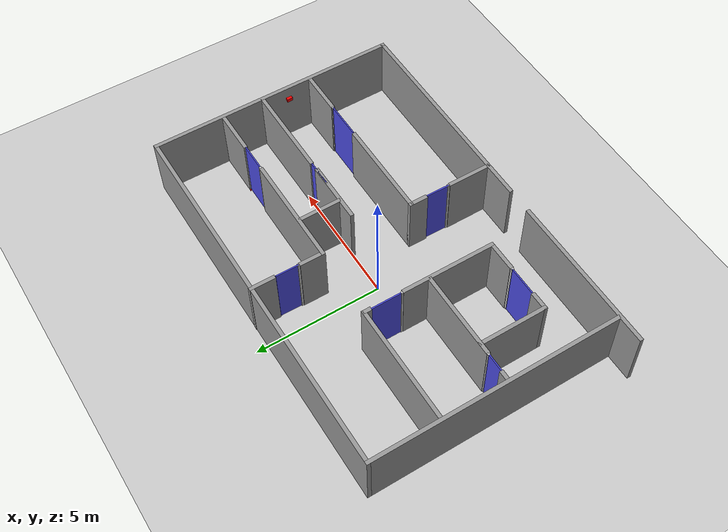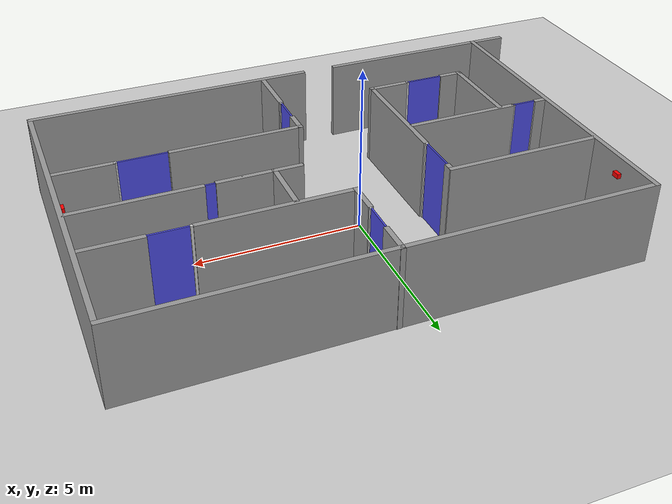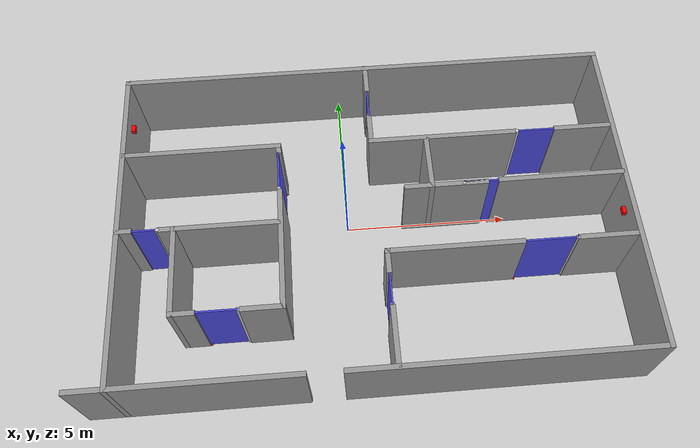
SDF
<sdf version="1.7">
 <world name="default">
  <light name="sun" type="directional">
   <pose>0 0 10 0 -0 0</pose>
   <diffuse>0.8 0.8 0.8 1</diffuse>
   <specular>0.2 0.2 0.2 1</specular>
   <attenuation>
    <range>1000</range>
    <constant>0.9</constant>
    <linear>0.01</linear>
    <quadratic>0.001</quadratic>
   </attenuation>
   <direction>-0.5 0.1 -0.9</direction>
   <spot><inner_angle>0</inner_angle><outer_angle>0</outer_angle><falloff>0</falloff></spot>
  </light>
  <model name="ground_plane">
   <static>1</static>
   <link name="link">
    <collision name="collision">
     <geometry><plane><normal>0 0 1</normal><size>100 100</size></plane></geometry>
     <surface><friction><ode><mu>100</mu><mu2>50</mu2></ode></friction></surface>
    </collision>
    <visual name="visual">
     <cast_shadows>0</cast_shadows>
     <geometry><plane><normal>0 0 1</normal><size>100 100</size></plane></geometry>
     <material>
      <script><uri>file://media/materials/scripts/gazebo.material</uri><name>Gazebo/Grey</name></script>
     </material>
    </visual>
   </link>
  </model>
  <gravity>0 0 -9.8</gravity>
  <magnetic_field>6e-06 2.3e-05 -4.2e-05</magnetic_field>
  <atmosphere type="adiabatic"/>
  <physics type="ode">
   <max_step_size>0.001</max_step_size>
   <real_time_factor>1</real_time_factor>
   <real_time_update_rate>1000</real_time_update_rate>
  </physics>
  <scene><ambient>0.4 0.4 0.4 1</ambient><background>0.7 0.7 0.7 1</background><shadows>1</shadows></scene>
  <spherical_coordinates>
   <surface_model>EARTH_WGS84</surface_model>
   <latitude_deg>0</latitude_deg>
   <longitude_deg>0</longitude_deg>
   <elevation>0</elevation>
   <heading_deg>0</heading_deg>
  </spherical_coordinates>
  <model name="Edificio_Tim">
   <pose>0.861582 -0.45356 0 0 -0 0</pose>
   <link name="Wall_10">
    <collision name="Wall_10_Collision">
     <geometry><box><size>15 0.15 2.5</size></box></geometry>
     <pose>0 0 1.25 0 -0 0</pose>
    </collision>
    <visual name="Wall_10_Visual">
     <pose>0 0 1.25 0 -0 0</pose>
     <geometry><box><size>15 0.15 2.5</size></box></geometry>
     <material>
      <script><uri>file://media/materials/scripts/gazebo.material</uri><name>Gazebo/Grey</name></script>
      <ambient>1 1 1 1</ambient>
     </material>
     <meta><layer>0</layer></meta>
    </visual>
    <pose>-0 4.91887 0 0 -0 0</pose>
   </link>
   <link name="Wall_11">
    <collision name="Wall_11_Collision">
     <geometry><box><size>10 0.15 2.5</size></box></geometry>
     <pose>0 0 1.25 0 -0 0</pose>
    </collision>
    <visual name="Wall_11_Visual">
     <pose>0 0 1.25 0 -0 0</pose>
     <geometry><box><size>10 0.15 2.5</size></box></geometry>
     <material>
      <script><uri>file://media/materials/scripts/gazebo.material</uri><name>Gazebo/Grey</name></script>
      <ambient>1 1 1 1</ambient>
     </material>
     <meta><layer>0</layer></meta>
    </visual>
    <pose>7.425 -0.006132 0 0 -0 -1.5708</pose>
   </link>
   <link name="Wall_14">
    <collision name="Wall_14_Collision">
     <geometry><box><size>8.75 0.15 2.5</size></box></geometry>
     <pose>0 0 1.25 0 -0 0</pose>
    </collision>
    <visual name="Wall_14_Visual">
     <pose>0 0 1.25 0 -0 0</pose>
     <geometry><box><size>8.75 0.15 2.5</size></box></geometry>
     <material>
      <script><uri>file://media/materials/scripts/gazebo.material</uri><name>Gazebo/Grey</name></script>
      <ambient>1 1 1 1</ambient>
     </material>
     <meta><layer>0</layer></meta>
    </visual>
    <pose>3.125 -4.93113 0 0 -0 3.14159</pose>
   </link>
   <link name="Wall_16">
    <collision name="Wall_16_Collision">
     <geometry><box><size>4.75 0.15 2.5</size></box></geometry>
     <pose>0 0 1.25 0 -0 0</pose>
    </collision>
    <visual name="Wall_16_Visual">
     <pose>0 0 1.25 0 -0 0</pose>
     <geometry><box><size>4.75 0.15 2.5</size></box></geometry>
     <material>
      <script><uri>file://media/materials/scripts/gazebo.material</uri><name>Gazebo/Grey</name></script>
      <ambient>1 1 1 1</ambient>
     </material>
     <meta><layer>0</layer></meta>
    </visual>
    <pose>-5.07129 2.18819 0 0 -0 0</pose>
   </link>
   <link name="Wall_17">
    <collision name="Wall_17_Collision">
     <geometry><box><size>0.3 0.15 2.5</size></box></geometry>
     <pose>-0.3 0 1.25 0 -0 0</pose>
    </collision>
    <visual name="Wall_17_Visual">
     <pose>-0.3 0 1.25 0 -0 0</pose>
     <geometry><box><size>0.3 0.15 2.5</size></box></geometry>
     <material>
      <script><uri>file://media/materials/scripts/gazebo.material</uri><name>Gazebo/Grey</name></script>
      <ambient>1 1 1 1</ambient>
     </material>
     <meta><layer>0</layer></meta>
    </visual>
    <pose>-2.77129 1.76319 0 0 -0 -1.5708</pose>
   </link>
   <link name="Wall_19">
    <collision name="Wall_19_Collision">
     <geometry><box><size>3.75 0.15 2.5</size></box></geometry>
     <pose>0 0 1.25 0 -0 0</pose>
    </collision>
    <visual name="Wall_19_Visual">
     <pose>0 0 1.25 0 -0 0</pose>
     <geometry><box><size>3.75 0.15 2.5</size></box></geometry>
     <material>
      <script><uri>file://media/materials/scripts/gazebo.material</uri><name>Gazebo/Grey</name></script>
      <ambient>1 1 1 1</ambient>
     </material>
     <meta><layer>0</layer></meta>
    </visual>
    <pose>-2.77141 -1.2034 0 0 -0 -1.5708</pose>
   </link>
   <link name="Wall_20">
    <collision name="Wall_20_Collision">
     <geometry><box><size>1.25 0.15 2.5</size></box></geometry>
     <pose>0 0 1.25 0 -0 0</pose>
    </collision>
    <visual name="Wall_20_Visual">
     <pose>0 0 1.25 0 -0 0</pose>
     <geometry><box><size>1.25 0.15 2.5</size></box></geometry>
     <material>
      <script><uri>file://media/materials/scripts/gazebo.material</uri><name>Gazebo/Grey</name></script>
      <ambient>1 1 1 1</ambient>
     </material>
     <meta><layer>0</layer></meta>
    </visual>
    <pose>-3.3214 -3.0034 0 0 -0 3.14159</pose>
   </link>
   <link name="Wall_22">
    <collision name="Wall_22_Collision">
     <geometry><box><size>0.75 0.15 2.5</size></box></geometry>
     <pose>0 0 1.25 0 -0 0</pose>
    </collision>
    <visual name="Wall_22_Visual">
     <pose>0 0 1.25 0 -0 0</pose>
     <geometry><box><size>0.75 0.15 2.5</size></box></geometry>
     <material>
      <script><uri>file://media/materials/scripts/gazebo.material</uri><name>Gazebo/Grey</name></script>
      <ambient>1 1 1 1</ambient>
     </material>
     <meta><layer>0</layer></meta>
    </visual>
    <pose>-5.52001 -3.00636 0 0 -0 3.14159</pose>
   </link>
   <link name="Wall_30">
    <collision name="Wall_30_Collision">
     <geometry><box><size>0.5 0.15 2.5</size></box></geometry>
     <pose>0 0 1.25 0 -0 0</pose>
    </collision>
    <visual name="Wall_30_Visual">
     <pose>0 0 1.25 0 -0 0</pose>
     <geometry><box><size>0.5 0.15 2.5</size></box></geometry>
     <material>
      <script><uri>file://media/materials/scripts/gazebo.material</uri><name>Gazebo/Grey</name></script>
      <ambient>1 1 1 1</ambient>
     </material>
     <meta><layer>0</layer></meta>
    </visual>
    <pose>-7.24876 -0.382847 0 0 -0 0</pose>
   </link>
   <link name="Wall_32">
    <collision name="Wall_32_Collision">
     <geometry><box><size>3.5 0.15 2.5</size></box></geometry>
     <pose>0 0 1.25 0 -0 0</pose>
    </collision>
    <visual name="Wall_32_Visual">
     <pose>0 0 1.25 0 -0 0</pose>
     <geometry><box><size>3.5 0.15 2.5</size></box></geometry>
     <material>
      <script><uri>file://media/materials/scripts/gazebo.material</uri><name>Gazebo/Grey</name></script>
      <ambient>1 1 1 1</ambient>
     </material>
     <meta><layer>0</layer></meta>
    </visual>
    <pose>-4.52359 -0.403337 0 0 -0 0</pose>
   </link>
   <link name="Wall_34">
    <collision name="Wall_34_Collision">
     <geometry><box><size>2.75 0.15 2.5</size></box></geometry>
     <pose>0 0 1.25 0 -0 0</pose>
    </collision>
    <visual name="Wall_34_Visual">
     <pose>0 0 1.25 0 -0 0</pose>
     <geometry><box><size>2.75 0.15 2.5</size></box></geometry>
     <material>
      <script><uri>file://media/materials/scripts/gazebo.material</uri><name>Gazebo/Grey</name></script>
      <ambient>1 1 1 1</ambient>
     </material>
     <meta><layer>0</layer></meta>
    </visual>
    <pose>-5.82001 -1.70636 0 0 -0 1.5708</pose>
   </link>
   <link name="Wall_36">
    <collision name="Wall_36_Collision">
     <geometry><box><size>1.75 0.15 2.5</size></box></geometry>
     <pose>0 0 1.25 0 -0 0</pose>
    </collision>
    <visual name="Wall_36_Visual">
     <pose>0 0 1.25 0 -0 0</pose>
     <geometry><box><size>1.75 0.15 2.5</size></box></geometry>
     <material>
      <script><uri>file://media/materials/scripts/gazebo.material</uri><name>Gazebo/Grey</name></script>
      <ambient>1 1 1 1</ambient>
     </material>
     <meta><layer>0</layer></meta>
    </visual>
    <pose>0.185286 -4.08079 0 0 -0 1.5708</pose>
   </link>
   <link name="Wall_40">
    <collision name="Wall_40_Collision">
     <geometry><box><size>0.75 0.15 2.5</size></box></geometry>
     <pose>0 0 1.25 0 -0 0</pose>
    </collision>
    <visual name="Wall_40_Visual">
     <pose>0 0 1.25 0 -0 0</pose>
     <geometry><box><size>0.75 0.15 2.5</size></box></geometry>
     <material>
      <script><uri>file://media/materials/scripts/gazebo.material</uri><name>Gazebo/Grey</name></script>
      <ambient>1 1 1 1</ambient>
     </material>
     <meta><layer>0</layer></meta>
    </visual>
    <pose>0.185286 -1.88079 0 0 -0 1.5708</pose>
   </link>
   <link name="Wall_43">
    <collision name="Wall_43_Collision">
     <geometry><box><size>1.75 0.15 2.5</size></box></geometry>
     <pose>0 0 1.25 0 -0 0</pose>
    </collision>
    <visual name="Wall_43_Visual">
     <pose>0 0 1.25 0 -0 0</pose>
     <geometry><box><size>1.75 0.15 2.5</size></box></geometry>
     <material>
      <script><uri>file://media/materials/scripts/gazebo.material</uri><name>Gazebo/Grey</name></script>
      <ambient>1 1 1 1</ambient>
     </material>
     <meta><layer>0</layer></meta>
    </visual>
    <pose>6.48529 -1.58079 0 0 -0 3.14159</pose>
   </link>
   <link name="Wall_45">
    <collision name="Wall_45_Collision">
     <geometry><box><size>4 0.15 2.5</size></box></geometry>
     <pose>0 0 1.25 0 -0 0</pose>
    </collision>
    <visual name="Wall_45_Visual">
     <pose>0 0 1.25 0 -0 0</pose>
     <geometry><box><size>4 0.15 2.5</size></box></geometry>
     <material>
      <script><uri>file://media/materials/scripts/gazebo.material</uri><name>Gazebo/Grey</name></script>
      <ambient>1 1 1 1</ambient>
     </material>
     <meta><layer>0</layer></meta>
    </visual>
    <pose>2.11029 -1.58079 0 0 -0 0</pose>
   </link>
   <link name="Wall_48">
    <collision name="Wall_48_Collision">
     <geometry><box><size>1 0.15 2.5</size></box></geometry>
     <pose>0 0 1.25 0 -0 0</pose>
    </collision>
    <visual name="Wall_48_Visual">
     <pose>0 0 1.25 0 -0 0</pose>
     <geometry><box><size>1 0.15 2.5</size></box></geometry>
     <material>
      <script><uri>file://media/materials/scripts/gazebo.material</uri><name>Gazebo/Grey</name></script>
      <ambient>1 1 1 1</ambient>
     </material>
     <meta><layer>0</layer></meta>
    </visual>
    <pose>0.045366 4.50613 0 0 -0 -1.5708</pose>
   </link>
   <link name="Wall_56">
    <collision name="Wall_56_Collision">
     <geometry><box><size>1 0.15 2.5</size></box></geometry>
     <pose>0 0 1.25 0 -0 0</pose>
    </collision>
    <visual name="Wall_56_Visual">
     <pose>0 0 1.25 0 -0 0</pose>
     <geometry><box><size>1 0.15 2.5</size></box></geometry>
     <material>
      <script><uri>file://media/materials/scripts/gazebo.material</uri><name>Gazebo/Grey</name></script>
      <ambient>1 1 1 1</ambient>
     </material>
     <meta><layer>0</layer></meta>
    </visual>
    <pose>0.027876 2.56474 0 0 -0 -1.5708</pose>
   </link>
   <link name="Wall_57">
    <collision name="Wall_57_Collision">
     <geometry><box><size>4.5 0.15 2.5</size></box></geometry>
     <pose>0 0 1.25 0 -0 0</pose>
    </collision>
    <visual name="Wall_57_Visual">
     <pose>0 0 1.25 0 -0 0</pose>
     <geometry><box><size>4.5 0.15 2.5</size></box></geometry>
     <material>
      <script><uri>file://media/materials/scripts/gazebo.material</uri><name>Gazebo/Grey</name></script>
      <ambient>1 1 1 1</ambient>
     </material>
     <meta><layer>0</layer></meta>
    </visual>
    <pose>2.20288 2.13973 0 0 -0 0</pose>
   </link>
   <link name="Wall_6">
    <collision name="Wall_6_Collision">
     <geometry><box><size>10 0.15 2.5</size></box></geometry>
     <pose>0 0 1.25 0 -0 0</pose>
    </collision>
    <visual name="Wall_6_Visual">
     <pose>0 0 1.25 0 -0 0</pose>
     <geometry><box><size>10 0.15 2.5</size></box></geometry>
     <material>
      <script><uri>file://media/materials/scripts/gazebo.material</uri><name>Gazebo/Grey</name></script>
      <ambient>1 1 1 1</ambient>
     </material>
     <meta><layer>0</layer></meta>
    </visual>
    <pose>-7.425 -0.006132 0 0 -0 -1.5708</pose>
   </link>
   <link name="Wall_60">
    <collision name="Wall_60_Collision">
     <geometry><box><size>1.75 0.15 2.5</size></box></geometry>
     <pose>0 0 1.25 0 -0 0</pose>
    </collision>
    <visual name="Wall_60_Visual">
     <pose>0 0 1.25 0 -0 0</pose>
     <geometry><box><size>1.75 0.15 2.5</size></box></geometry>
     <material>
      <script><uri>file://media/materials/scripts/gazebo.material</uri><name>Gazebo/Grey</name></script>
      <ambient>1 1 1 1</ambient>
     </material>
     <meta><layer>0</layer></meta>
    </visual>
    <pose>6.49466 2.15021 0 0 -0 0</pose>
   </link>
   <link name="Wall_62">
    <collision name="Wall_62_Collision">
     <geometry><box><size>1.75 0.15 2.5</size></box></geometry>
     <pose>0 0 1.25 0 -0 0</pose>
    </collision>
    <visual name="Wall_62_Visual">
     <pose>0 0 1.25 0 -0 0</pose>
     <geometry><box><size>1.75 0.15 2.5</size></box></geometry>
     <material>
      <script><uri>file://media/materials/scripts/gazebo.material</uri><name>Gazebo/Grey</name></script>
      <ambient>1 1 1 1</ambient>
     </material>
     <meta><layer>0</layer></meta>
    </visual>
    <pose>1.68943 1.24527 0 0 -0 -1.5708</pose>
   </link>
   <link name="Wall_63">
    <collision name="Wall_63_Collision">
     <geometry><box><size>2.5 0.15 2.5</size></box></geometry>
     <pose>0 0 1.25 0 -0 0</pose>
    </collision>
    <visual name="Wall_63_Visual">
     <pose>0 0 1.25 0 -0 0</pose>
     <geometry><box><size>2.5 0.15 2.5</size></box></geometry>
     <material>
      <script><uri>file://media/materials/scripts/gazebo.material</uri><name>Gazebo/Grey</name></script>
      <ambient>1 1 1 1</ambient>
     </material>
     <meta><layer>0</layer></meta>
    </visual>
    <pose>2.11443 0.445272 0 0 -0 0</pose>
   </link>
   <link name="Wall_67">
    <collision name="Wall_67_Collision">
     <geometry><box><size>3.75 0.15 2.5</size></box></geometry>
     <pose>0 0 1.25 0 -0 0</pose>
    </collision>
    <visual name="Wall_67_Visual">
     <pose>0 0 1.25 0 -0 0</pose>
     <geometry><box><size>3.75 0.15 2.5</size></box></geometry>
     <material>
      <script><uri>file://media/materials/scripts/gazebo.material</uri><name>Gazebo/Grey</name></script>
      <ambient>1 1 1 1</ambient>
     </material>
     <meta><layer>0</layer></meta>
    </visual>
    <pose>5.53577 0.471166 0 0 -0 0</pose>
   </link>
   <link name="Wall_8">
    <collision name="Wall_8_Collision">
     <geometry><box><size>6.3 0.15 2.5</size></box></geometry>
     <pose>0 0 1.25 0 -0 0</pose>
    </collision>
    <visual name="Wall_8_Visual">
     <pose>0 0 1.25 0 -0 0</pose>
     <geometry><box><size>6.3 0.15 2.5</size></box></geometry>
     <material>
      <script><uri>file://media/materials/scripts/gazebo.material</uri><name>Gazebo/Grey</name></script>
      <ambient>1 1 1 1</ambient>
     </material>
     <meta><layer>0</layer></meta>
    </visual>
    <pose>-5.375 -4.93113 0 0 -0 0</pose>
   </link>
   <static>1</static>
  </model>
  <model name="Lidar_8">
   <link name="link_1">
    <inertial>
     <mass>0.00014111</mass>
     <inertia><ixx>7e-08</ixx><ixy>0</ixy><ixz>0</ixz><iyy>7e-08</iyy><iyz>0</iyz><izz>6e-08</izz></inertia>
    </inertial>
    <visual name="visual">
     <geometry><box><size>0.048286 0.048861 0.059852</size></box></geometry>
     <material>
      <lighting>1</lighting>
      <script><uri>file://media/materials/scripts/gazebo.material</uri><name>Gazebo/Grey</name></script>
      <shader type="pixel"><normal_map>__default__</normal_map></shader>
      <ambient>1 0 0 1</ambient>
      <diffuse>0.7 0.7 0.7 1</diffuse>
      <specular>0.01 0.01 0.01 1</specular>
      <emissive>0 0 0 1</emissive>
     </material>
    </visual>
    <collision name="collision">
     <geometry><box><size>0.048286 0.048861 0.059852</size></box></geometry>
     <surface>
      <friction>
       <ode><mu>1</mu><mu2>1</mu2><fdir1>0 0 0</fdir1><slip1>0</slip1><slip2>0</slip2></ode>
       <torsional>
        <coefficient>1</coefficient>
        <patch_radius>0</patch_radius>
        <surface_radius>0</surface_radius>
        <use_patch_radius>1</use_patch_radius>
        <ode><slip>0</slip></ode>
       </torsional>
      </friction>
      <bounce><restitution_coefficient>0</restitution_coefficient><threshold>1e+06</threshold></bounce>
      <contact>
       <collide_without_contact>0</collide_without_contact>
       <collide_without_contact_bitmask>1</collide_without_contact_bitmask>
       <collide_bitmask>1</collide_bitmask>
       <ode>
        <soft_cfm>0</soft_cfm>
        <soft_erp>0.2</soft_erp>
        <kp>1e+13</kp>
        <kd>1</kd>
        <max_vel>0.01</max_vel>
        <min_depth>0</min_depth>
       </ode>
       <bullet>
        <split_impulse>1</split_impulse>
        <split_impulse_penetration_threshold>-0.01</split_impulse_penetration_threshold>
        <soft_cfm>0</soft_cfm>
        <soft_erp>0.2</soft_erp>
        <kp>1e+13</kp>
        <kd>1</kd>
       </bullet>
      </contact>
     </surface>
    </collision>
   </link>
   <static>0</static>
   <pose>-4.25776 -3.50341 0.029926 -1e-06 -0 -0.001906</pose>
  </model>
  <model name="Lidar_1">
   <link name="link_1">
    <inertial>
     <mass>0.00014111</mass>
     <inertia><ixx>7e-08</ixx><ixy>0</ixy><ixz>0</ixz><iyy>7e-08</iyy><iyz>0</iyz><izz>6e-08</izz></inertia>
    </inertial>
    <visual name="visual">
     <geometry><box><size>0.048286 0.048861 0.059852</size></box></geometry>
     <material>
      <lighting>1</lighting>
      <script><uri>file://media/materials/scripts/gazebo.material</uri><name>Gazebo/Grey</name></script>
      <shader type="pixel"><normal_map>__default__</normal_map></shader>
      <ambient>1 0 0 1</ambient>
      <diffuse>0.7 0.7 0.7 1</diffuse>
      <specular>0.01 0.01 0.01 1</specular>
      <emissive>0 0 0 1</emissive>
     </material>
    </visual>
    <collision name="collision">
     <geometry><box><size>0.048286 0.048861 0.059852</size></box></geometry>
     <surface>
      <friction>
       <ode><mu>1</mu><mu2>1</mu2><fdir1>0 0 0</fdir1><slip1>0</slip1><slip2>0</slip2></ode>
       <torsional>
        <coefficient>1</coefficient>
        <patch_radius>0</patch_radius>
        <surface_radius>0</surface_radius>
        <use_patch_radius>1</use_patch_radius>
        <ode><slip>0</slip></ode>
       </torsional>
      </friction>
      <bounce><restitution_coefficient>0</restitution_coefficient><threshold>1e+06</threshold></bounce>
      <contact>
       <collide_without_contact>0</collide_without_contact>
       <collide_without_contact_bitmask>1</collide_without_contact_bitmask>
       <collide_bitmask>1</collide_bitmask>
       <ode>
        <soft_cfm>0</soft_cfm>
        <soft_erp>0.2</soft_erp>
        <kp>1e+13</kp>
        <kd>1</kd>
        <max_vel>0.01</max_vel>
        <min_depth>0</min_depth>
       </ode>
       <bullet>
        <split_impulse>1</split_impulse>
        <split_impulse_penetration_threshold>-0.01</split_impulse_penetration_threshold>
        <soft_cfm>0</soft_cfm>
        <soft_erp>0.2</soft_erp>
        <kp>1e+13</kp>
        <kd>1</kd>
       </bullet>
      </contact>
     </surface>
    </collision>
   </link>
   <static>0</static>
   <pose>1.09749 -2.73381 0.029924 6.1e-05 -0.000135 -1.56366</pose>
  </model>
  <model name="Lidar_3">
   <link name="link_1">
    <inertial>
     <mass>0.00014111</mass>
     <inertia><ixx>7e-08</ixx><ixy>0</ixy><ixz>0</ixz><iyy>7e-08</iyy><iyz>0</iyz><izz>6e-08</izz></inertia>
    </inertial>
    <visual name="visual">
     <geometry><box><size>0.048286 0.048861 0.059852</size></box></geometry>
     <material>
      <lighting>1</lighting>
      <script><uri>file://media/materials/scripts/gazebo.material</uri><name>Gazebo/Grey</name></script>
      <shader type="pixel"><normal_map>__default__</normal_map></shader>
      <ambient>1 0 0 1</ambient>
      <diffuse>0.7 0.7 0.7 1</diffuse>
      <specular>0.01 0.01 0.01 1</specular>
      <emissive>0 0 0 1</emissive>
     </material>
    </visual>
    <collision name="collision">
     <geometry><box><size>0.048286 0.048861 0.059852</size></box></geometry>
     <surface>
      <friction>
       <ode><mu>1</mu><mu2>1</mu2><fdir1>0 0 0</fdir1><slip1>0</slip1><slip2>0</slip2></ode>
       <torsional>
        <coefficient>1</coefficient>
        <patch_radius>0</patch_radius>
        <surface_radius>0</surface_radius>
        <use_patch_radius>1</use_patch_radius>
        <ode><slip>0</slip></ode>
       </torsional>
      </friction>
      <bounce><restitution_coefficient>0</restitution_coefficient><threshold>1e+06</threshold></bounce>
      <contact>
       <collide_without_contact>0</collide_without_contact>
       <collide_without_contact_bitmask>1</collide_without_contact_bitmask>
       <collide_bitmask>1</collide_bitmask>
       <ode>
        <soft_cfm>0</soft_cfm>
        <soft_erp>0.2</soft_erp>
        <kp>1e+13</kp>
        <kd>1</kd>
        <max_vel>0.01</max_vel>
        <min_depth>0</min_depth>
       </ode>
       <bullet>
        <split_impulse>1</split_impulse>
        <split_impulse_penetration_threshold>-0.01</split_impulse_penetration_threshold>
        <soft_cfm>0</soft_cfm>
        <soft_erp>0.2</soft_erp>
        <kp>1e+13</kp>
        <kd>1</kd>
       </bullet>
      </contact>
     </surface>
    </collision>
   </link>
   <static>0</static>
   <pose>4.48897 -0.039578 0.029924 6.1e-05 0.000136 3.11957</pose>
  </model>
  <model name="Lidar_4">
   <link name="link_1">
    <inertial>
     <mass>0.00014111</mass>
     <inertia><ixx>7e-08</ixx><ixy>0</ixy><ixz>0</ixz><iyy>7e-08</iyy><iyz>0</iyz><izz>6e-08</izz></inertia>
    </inertial>
    <visual name="visual">
     <geometry><box><size>0.048286 0.048861 0.059852</size></box></geometry>
     <material>
      <lighting>1</lighting>
      <script><uri>file://media/materials/scripts/gazebo.material</uri><name>Gazebo/Grey</name></script>
      <shader type="pixel"><normal_map>__default__</normal_map></shader>
      <ambient>1 0 0 1</ambient>
      <diffuse>0.7 0.7 0.7 1</diffuse>
      <specular>0.01 0.01 0.01 1</specular>
      <emissive>0 0 0 1</emissive>
     </material>
    </visual>
    <collision name="collision">
     <geometry><box><size>0.048286 0.048861 0.059852</size></box></geometry>
     <surface>
      <friction>
       <ode><mu>1</mu><mu2>1</mu2><fdir1>0 0 0</fdir1><slip1>0</slip1><slip2>0</slip2></ode>
       <torsional>
        <coefficient>1</coefficient>
        <patch_radius>0</patch_radius>
        <surface_radius>0</surface_radius>
        <use_patch_radius>1</use_patch_radius>
        <ode><slip>0</slip></ode>
       </torsional>
      </friction>
      <bounce><restitution_coefficient>0</restitution_coefficient><threshold>1e+06</threshold></bounce>
      <contact>
       <collide_without_contact>0</collide_without_contact>
       <collide_without_contact_bitmask>1</collide_without_contact_bitmask>
       <collide_bitmask>1</collide_bitmask>
       <ode>
        <soft_cfm>0</soft_cfm>
        <soft_erp>0.2</soft_erp>
        <kp>1e+13</kp>
        <kd>1</kd>
        <max_vel>0.01</max_vel>
        <min_depth>0</min_depth>
       </ode>
       <bullet>
        <split_impulse>1</split_impulse>
        <split_impulse_penetration_threshold>-0.01</split_impulse_penetration_threshold>
        <soft_cfm>0</soft_cfm>
        <soft_erp>0.2</soft_erp>
        <kp>1e+13</kp>
        <kd>1</kd>
       </bullet>
      </contact>
     </surface>
    </collision>
   </link>
   <static>0</static>
   <pose>6.45469 1.75553 0.029921 -8.9e-05 -0.00011 3.13332</pose>
  </model>
  <model name="Lidar_5">
   <link name="link_1">
    <inertial>
     <mass>0.00014111</mass>
     <inertia><ixx>7e-08</ixx><ixy>0</ixy><ixz>0</ixz><iyy>7e-08</iyy><iyz>0</iyz><izz>6e-08</izz></inertia>
    </inertial>
    <visual name="visual">
     <geometry><box><size>0.048286 0.048861 0.059852</size></box></geometry>
     <material>
      <lighting>1</lighting>
      <script><uri>file://media/materials/scripts/gazebo.material</uri><name>Gazebo/Grey</name></script>
      <shader type="pixel"><normal_map>__default__</normal_map></shader>
      <ambient>1 0 0 1</ambient>
      <diffuse>0.7 0.7 0.7 1</diffuse>
      <specular>0.01 0.01 0.01 1</specular>
      <emissive>0 0 0 1</emissive>
     </material>
    </visual>
    <collision name="collision">
     <geometry><box><size>0.048286 0.048861 0.059852</size></box></geometry>
     <surface>
      <friction>
       <ode><mu>1</mu><mu2>1</mu2><fdir1>0 0 0</fdir1><slip1>0</slip1><slip2>0</slip2></ode>
       <torsional>
        <coefficient>1</coefficient>
        <patch_radius>0</patch_radius>
        <surface_radius>0</surface_radius>
        <use_patch_radius>1</use_patch_radius>
        <ode><slip>0</slip></ode>
       </torsional>
      </friction>
      <bounce><restitution_coefficient>0</restitution_coefficient><threshold>1e+06</threshold></bounce>
      <contact>
       <collide_without_contact>0</collide_without_contact>
       <collide_without_contact_bitmask>1</collide_without_contact_bitmask>
       <collide_bitmask>1</collide_bitmask>
       <ode>
        <soft_cfm>0</soft_cfm>
        <soft_erp>0.2</soft_erp>
        <kp>1e+13</kp>
        <kd>1</kd>
        <max_vel>0.01</max_vel>
        <min_depth>0</min_depth>
       </ode>
       <bullet>
        <split_impulse>1</split_impulse>
        <split_impulse_penetration_threshold>-0.01</split_impulse_penetration_threshold>
        <soft_cfm>0</soft_cfm>
        <soft_erp>0.2</soft_erp>
        <kp>1e+13</kp>
        <kd>1</kd>
       </bullet>
      </contact>
     </surface>
    </collision>
   </link>
   <static>0</static>
   <pose>0.955852 3.52726 0.029921 8.9e-05 -0.00011 -1.57506</pose>
  </model>
  <model name="Lidar_6">
   <link name="link_1">
    <inertial>
     <mass>0.00014111</mass>
     <inertia><ixx>7e-08</ixx><ixy>0</ixy><ixz>0</ixz><iyy>7e-08</iyy><iyz>0</iyz><izz>6e-08</izz></inertia>
    </inertial>
    <visual name="visual">
     <geometry><box><size>0.048286 0.048861 0.059852</size></box></geometry>
     <material>
      <lighting>1</lighting>
      <script><uri>file://media/materials/scripts/gazebo.material</uri><name>Gazebo/Grey</name></script>
      <shader type="pixel"><normal_map>__default__</normal_map></shader>
      <ambient>1 0 0 1</ambient>
      <diffuse>0.7 0.7 0.7 1</diffuse>
      <specular>0.01 0.01 0.01 1</specular>
      <emissive>0 0 0 1</emissive>
     </material>
    </visual>
    <collision name="collision">
     <geometry><box><size>0.048286 0.048861 0.059852</size></box></geometry>
     <surface>
      <friction>
       <ode><mu>1</mu><mu2>1</mu2><fdir1>0 0 0</fdir1><slip1>0</slip1><slip2>0</slip2></ode>
       <torsional>
        <coefficient>1</coefficient>
        <patch_radius>0</patch_radius>
        <surface_radius>0</surface_radius>
        <use_patch_radius>1</use_patch_radius>
        <ode><slip>0</slip></ode>
       </torsional>
      </friction>
      <bounce><restitution_coefficient>0</restitution_coefficient><threshold>1e+06</threshold></bounce>
      <contact>
       <collide_without_contact>0</collide_without_contact>
       <collide_without_contact_bitmask>1</collide_without_contact_bitmask>
       <collide_bitmask>1</collide_bitmask>
       <ode>
        <soft_cfm>0</soft_cfm>
        <soft_erp>0.2</soft_erp>
        <kp>1e+13</kp>
        <kd>1</kd>
        <max_vel>0.01</max_vel>
        <min_depth>0</min_depth>
       </ode>
       <bullet>
        <split_impulse>1</split_impulse>
        <split_impulse_penetration_threshold>-0.01</split_impulse_penetration_threshold>
        <soft_cfm>0</soft_cfm>
        <soft_erp>0.2</soft_erp>
        <kp>1e+13</kp>
        <kd>1</kd>
       </bullet>
      </contact>
     </surface>
    </collision>
   </link>
   <static>0</static>
   <pose>-1.90196 1.4346 0.029926 0 1e-06 -1.57737</pose>
  </model>
  <model name="Lidar_2">
   <link name="link_1">
    <inertial>
     <mass>0.00014111</mass>
     <inertia><ixx>7e-08</ixx><ixy>0</ixy><ixz>0</ixz><iyy>7e-08</iyy><iyz>0</iyz><izz>6e-08</izz></inertia>
    </inertial>
    <visual name="visual">
     <geometry><box><size>0.048286 0.048861 0.059852</size></box></geometry>
     <material>
      <lighting>1</lighting>
      <script><uri>file://media/materials/scripts/gazebo.material</uri><name>Gazebo/Grey</name></script>
      <shader type="pixel"><normal_map>__default__</normal_map></shader>
      <ambient>1 0 0 1</ambient>
      <diffuse>0.7 0.7 0.7 1</diffuse>
      <specular>0.01 0.01 0.01 1</specular>
      <emissive>0 0 0 1</emissive>
     </material>
    </visual>
    <collision name="collision">
     <geometry><box><size>0.048286 0.048861 0.059852</size></box></geometry>
     <surface>
      <friction>
       <ode><mu>1</mu><mu2>1</mu2><fdir1>0 0 0</fdir1><slip1>0</slip1><slip2>0</slip2></ode>
       <torsional>
        <coefficient>1</coefficient>
        <patch_radius>0</patch_radius>
        <surface_radius>0</surface_radius>
        <use_patch_radius>1</use_patch_radius>
        <ode><slip>0</slip></ode>
       </torsional>
      </friction>
      <bounce><restitution_coefficient>0</restitution_coefficient><threshold>1e+06</threshold></bounce>
      <contact>
       <collide_without_contact>0</collide_without_contact>
       <collide_without_contact_bitmask>1</collide_without_contact_bitmask>
       <collide_bitmask>1</collide_bitmask>
       <ode>
        <soft_cfm>0</soft_cfm>
        <soft_erp>0.2</soft_erp>
        <kp>1e+13</kp>
        <kd>1</kd>
        <max_vel>0.01</max_vel>
        <min_depth>0</min_depth>
       </ode>
       <bullet>
        <split_impulse>1</split_impulse>
        <split_impulse_penetration_threshold>-0.01</split_impulse_penetration_threshold>
        <soft_cfm>0</soft_cfm>
        <soft_erp>0.2</soft_erp>
        <kp>1e+13</kp>
        <kd>1</kd>
       </bullet>
      </contact>
     </surface>
    </collision>
   </link>
   <static>0</static>
   <pose>4.99634 -2.0856 0.029921 -8.9e-05 -0.00011 -0.006261</pose>
  </model>
  <model name="Lidar_7">
   <link name="link_1">
    <inertial>
     <mass>0.00014111</mass>
     <inertia><ixx>7e-08</ixx><ixy>0</ixy><ixz>0</ixz><iyy>7e-08</iyy><iyz>0</iyz><izz>6e-08</izz></inertia>
    </inertial>
    <visual name="visual">
     <geometry><box><size>0.048286 0.048861 0.059852</size></box></geometry>
     <material>
      <lighting>1</lighting>
      <script><uri>file://media/materials/scripts/gazebo.material</uri><name>Gazebo/Grey</name></script>
      <shader type="pixel"><normal_map>__default__</normal_map></shader>
      <ambient>1 0 0 1</ambient>
      <diffuse>0.7 0.7 0.7 1</diffuse>
      <specular>0.01 0.01 0.01 1</specular>
      <emissive>0 0 0 1</emissive>
     </material>
    </visual>
    <collision name="collision">
     <geometry><box><size>0.048286 0.048861 0.059852</size></box></geometry>
     <surface>
      <friction>
       <ode><mu>1</mu><mu2>1</mu2><fdir1>0 0 0</fdir1><slip1>0</slip1><slip2>0</slip2></ode>
       <torsional>
        <coefficient>1</coefficient>
        <patch_radius>0</patch_radius>
        <surface_radius>0</surface_radius>
        <use_patch_radius>1</use_patch_radius>
        <ode><slip>0</slip></ode>
       </torsional>
      </friction>
      <bounce><restitution_coefficient>0</restitution_coefficient><threshold>1e+06</threshold></bounce>
      <contact>
       <collide_without_contact>0</collide_without_contact>
       <collide_without_contact_bitmask>1</collide_without_contact_bitmask>
       <collide_bitmask>1</collide_bitmask>
       <ode>
        <soft_cfm>0</soft_cfm>
        <soft_erp>0.2</soft_erp>
        <kp>1e+13</kp>
        <kd>1</kd>
        <max_vel>0.01</max_vel>
        <min_depth>0</min_depth>
       </ode>
       <bullet>
        <split_impulse>1</split_impulse>
        <split_impulse_penetration_threshold>-0.01</split_impulse_penetration_threshold>
        <soft_cfm>0</soft_cfm>
        <soft_erp>0.2</soft_erp>
        <kp>1e+13</kp>
        <kd>1</kd>
       </bullet>
      </contact>
     </surface>
    </collision>
   </link>
   <static>0</static>
   <pose>-6.11261 -0.796443 0.029926 -0 -0 -0.009822</pose>
  </model>
  <model name="Camera_1">
   <link name="link_1">
    <inertial>
     <mass>0.00014152</mass>
     <inertia><ixx>8.3e-07</ixx><ixy>0</ixy><ixz>0</ixz><iyy>4e-07</iyy><iyz>0</iyz><izz>7.7e-07</izz></inertia>
    </inertial>
    <gravity>0</gravity>
    <visual name="visual">
     <geometry><box><size>0.119276 0.225925 0.14044</size></box></geometry>
     <material>
      <lighting>1</lighting>
      <script><uri>file://media/materials/scripts/gazebo.material</uri><name>Gazebo/Grey</name></script>
      <shader type="pixel"><normal_map>__default__</normal_map></shader>
      <ambient>1 0 0 1</ambient>
      <diffuse>0.7 0.7 0.7 1</diffuse>
      <specular>0.01 0.01 0.01 1</specular>
      <emissive>0 0 0 1</emissive>
     </material>
    </visual>
    <collision name="collision">
     <geometry><box><size>0.119276 0.225925 0.14044</size></box></geometry>
     <surface>
      <friction>
       <ode><mu>1</mu><mu2>1</mu2><fdir1>0 0 0</fdir1><slip1>0</slip1><slip2>0</slip2></ode>
       <torsional>
        <coefficient>1</coefficient>
        <patch_radius>0</patch_radius>
        <surface_radius>0</surface_radius>
        <use_patch_radius>1</use_patch_radius>
        <ode><slip>0</slip></ode>
       </torsional>
      </friction>
      <bounce><restitution_coefficient>0</restitution_coefficient><threshold>1e+06</threshold></bounce>
      <contact>
       <collide_without_contact>0</collide_without_contact>
       <collide_without_contact_bitmask>1</collide_without_contact_bitmask>
       <collide_bitmask>1</collide_bitmask>
       <ode>
        <soft_cfm>0</soft_cfm>
        <soft_erp>0.2</soft_erp>
        <kp>1e+13</kp>
        <kd>1</kd>
        <max_vel>0.01</max_vel>
        <min_depth>0</min_depth>
       </ode>
       <bullet>
        <split_impulse>1</split_impulse>
        <split_impulse_penetration_threshold>-0.01</split_impulse_penetration_threshold>
        <soft_cfm>0</soft_cfm>
        <soft_erp>0.2</soft_erp>
        <kp>1e+13</kp>
        <kd>1</kd>
       </bullet>
      </contact>
     </surface>
    </collision>
    <sensor name="camera_sensor1" type="camera">
     <update_rate>30</update_rate>
     <camera>
      <horizontal_fov>2.5</horizontal_fov>
      <image><width>800</width><height>600</height><format>R8G8B8</format></image>
      <clip><near>0.1</near><far>100</far></clip>
      <distortion><k1>-0.3</k1><k2>0.1</k2><p1>0</p1><p2>0</p2></distortion>
     </camera>
     <plugin name="camera_plugin" filename="libcamera_plugin.so"/>
    </sensor>
   </link>
   <static>0</static>
   <pose>8.13503 -1.04662 2 0 0 -3.14</pose>
  </model>
  <model name="Camera_2">
   <link name="link_1">
    <inertial>
     <mass>0.00014152</mass>
     <inertia><ixx>8.3e-07</ixx><ixy>0</ixy><ixz>0</ixz><iyy>4e-07</iyy><iyz>0</iyz><izz>7.7e-07</izz></inertia>
    </inertial>
    <gravity>0</gravity>
    <visual name="visual">
     <geometry><box><size>0.119276 0.225925 0.14044</size></box></geometry>
     <material>
      <lighting>1</lighting>
      <script><uri>file://media/materials/scripts/gazebo.material</uri><name>Gazebo/Grey</name></script>
      <shader type="pixel"><normal_map>__default__</normal_map></shader>
      <ambient>1 0 0 1</ambient>
      <diffuse>0.7 0.7 0.7 1</diffuse>
      <specular>0.01 0.01 0.01 1</specular>
      <emissive>0 0 0 1</emissive>
     </material>
    </visual>
    <collision name="collision">
     <geometry><box><size>0.119276 0.225925 0.14044</size></box></geometry>
     <surface>
      <friction>
       <ode><mu>1</mu><mu2>1</mu2><fdir1>0 0 0</fdir1><slip1>0</slip1><slip2>0</slip2></ode>
       <torsional>
        <coefficient>1</coefficient>
        <patch_radius>0</patch_radius>
        <surface_radius>0</surface_radius>
        <use_patch_radius>1</use_patch_radius>
        <ode><slip>0</slip></ode>
       </torsional>
      </friction>
      <bounce><restitution_coefficient>0</restitution_coefficient><threshold>1e+06</threshold></bounce>
      <contact>
       <collide_without_contact>0</collide_without_contact>
       <collide_without_contact_bitmask>1</collide_without_contact_bitmask>
       <collide_bitmask>1</collide_bitmask>
       <ode>
        <soft_cfm>0</soft_cfm>
        <soft_erp>0.2</soft_erp>
        <kp>1e+13</kp>
        <kd>1</kd>
        <max_vel>0.01</max_vel>
        <min_depth>0</min_depth>
       </ode>
       <bullet>
        <split_impulse>1</split_impulse>
        <split_impulse_penetration_threshold>-0.01</split_impulse_penetration_threshold>
        <soft_cfm>0</soft_cfm>
        <soft_erp>0.2</soft_erp>
        <kp>1e+13</kp>
        <kd>1</kd>
       </bullet>
      </contact>
     </surface>
    </collision>
    <sensor name="camera_sensor2" type="camera">
     <update_rate>30</update_rate>
     <camera>
      <horizontal_fov>2.5</horizontal_fov>
      <image><width>800</width><height>600</height><format>R8G8B8</format></image>
      <clip><near>0.1</near><far>100</far></clip>
      <distortion><k1>-0.3</k1><k2>0.1</k2><p1>0</p1><p2>0</p2></distortion>
     </camera>
     <plugin name="camera_plugin" filename="libcamera_plugin.so"/>
    </sensor>
   </link>
   <static>0</static>
   <pose>-6.42835 3.03849 2 0 -0 0</pose>
  </model>
  <model name="door_1">
   <link name="door_frame">
    <pose>0.25 -0 1.25 0 -0 0</pose>
    <kinematic>1</kinematic>
    <inertial>
     <inertia><ixx>1</ixx><ixy>0</ixy><ixz>0</ixz><iyy>1</iyy><iyz>0</iyz><izz>1</izz></inertia>
     <mass>1</mass>
    </inertial>
    <visual name="frame_visual">
     <geometry><box><size>0.1 0.1 2.5</size></box></geometry>
     <material>
      <ambient>0.7 0.7 0.7 1</ambient>
      <diffuse>0.8 0.8 0.8 1</diffuse>
      <shader type="pixel"/>
      <script><name>ModelPreview_1::door_frame::frame_visual_MATERIAL_</name><uri>__default__</uri></script>
     </material>
    </visual>
    <collision name="frame_collision">
     <geometry><box><size>0.1 0.1 2.5</size></box></geometry>
     <surface>
      <friction>
       <ode><mu>1</mu><mu2>1</mu2><fdir1>0 0 0</fdir1><slip1>0</slip1><slip2>0</slip2></ode>
       <torsional>
        <coefficient>1</coefficient>
        <patch_radius>0</patch_radius>
        <surface_radius>0</surface_radius>
        <use_patch_radius>1</use_patch_radius>
        <ode><slip>0</slip></ode>
       </torsional>
      </friction>
      <bounce><restitution_coefficient>0</restitution_coefficient><threshold>1e+06</threshold></bounce>
      <contact>
       <collide_without_contact>0</collide_without_contact>
       <collide_without_contact_bitmask>1</collide_without_contact_bitmask>
       <collide_bitmask>1</collide_bitmask>
       <ode>
        <soft_cfm>0</soft_cfm>
        <soft_erp>0.2</soft_erp>
        <kp>1e+13</kp>
        <kd>1</kd>
        <max_vel>0.01</max_vel>
        <min_depth>0</min_depth>
       </ode>
       <bullet>
        <split_impulse>1</split_impulse>
        <split_impulse_penetration_threshold>-0.01</split_impulse_penetration_threshold>
        <soft_cfm>0</soft_cfm>
        <soft_erp>0.2</soft_erp>
        <kp>1e+13</kp>
        <kd>1</kd>
       </bullet>
      </contact>
     </surface>
    </collision>
   </link>
   <link name="door">
    <kinematic>1</kinematic>
    <pose>-0.195697 -0 1.25 0 -0 0</pose>
    <inertial>
     <inertia>
      <ixx>0.971443</ixx>
      <ixy>0</ixy>
      <ixz>0</ixz>
      <iyy>1.10607</iyy>
      <iyz>0</iyz>
      <izz>0.135403</izz>
     </inertia>
     <mass>1.86443</mass>
    </inertial>
    <visual name="door_visual">
     <geometry><box><size>0.932199 0.05 2.5</size></box></geometry>
     <material>
      <ambient>0.2 0.2 0.8 1</ambient>
      <diffuse>0.3 0.3 0.9 1</diffuse>
      <shader type="pixel"/>
      <script><name>ModelPreview_1::door::door_visual_MATERIAL_</name><uri>__default__</uri></script>
     </material>
    </visual>
    <collision name="door_collision">
     <geometry><box><size>0.932199 0.05 2.5</size></box></geometry>
     <surface>
      <friction>
       <ode><mu>1</mu><mu2>1</mu2><fdir1>0 0 0</fdir1><slip1>0</slip1><slip2>0</slip2></ode>
       <torsional>
        <coefficient>1</coefficient>
        <patch_radius>0</patch_radius>
        <surface_radius>0</surface_radius>
        <use_patch_radius>1</use_patch_radius>
        <ode><slip>0</slip></ode>
       </torsional>
      </friction>
      <bounce><restitution_coefficient>0</restitution_coefficient><threshold>1e+06</threshold></bounce>
      <contact>
       <collide_without_contact>0</collide_without_contact>
       <collide_without_contact_bitmask>1</collide_without_contact_bitmask>
       <collide_bitmask>1</collide_bitmask>
       <ode>
        <soft_cfm>0</soft_cfm>
        <soft_erp>0.2</soft_erp>
        <kp>1e+13</kp>
        <kd>1</kd>
        <max_vel>0.01</max_vel>
        <min_depth>0</min_depth>
       </ode>
       <bullet>
        <split_impulse>1</split_impulse>
        <split_impulse_penetration_threshold>-0.01</split_impulse_penetration_threshold>
        <soft_cfm>0</soft_cfm>
        <soft_erp>0.2</soft_erp>
        <kp>1e+13</kp>
        <kd>1</kd>
       </bullet>
      </contact>
     </surface>
    </collision>
   </link>
   <joint name="door_joint" type="prismatic">
    <parent>door_frame</parent>
    <child>door</child>
    <axis>
     <xyz>1 0 0</xyz>
     <limit><lower>0</lower><upper>1</upper><effort>-1</effort><velocity>-1</velocity></limit>
     <dynamics>
      <spring_reference>0</spring_reference>
      <spring_stiffness>0</spring_stiffness>
      <damping>0</damping>
      <friction>0</friction>
     </dynamics>
    </axis>
    <physics>
     <ode><limit><cfm>0</cfm><erp>0.2</erp></limit><suspension><cfm>0</cfm><erp>0.2</erp></suspension></ode>
    </physics>
   </joint>
   <static>0</static>
   <plugin name="door_control_plugin" filename="libdoor_control_plugin.so">
    <door_joint>door_joint</door_joint>
    <speed>1.0</speed>
    <open_target>1.0</open_target>
    <close_target>0.0</close_target>
   </plugin>
   <pose>1.04541 -3.38243 0 0 0 -1.57622</pose>
  </model>
  <model name="door_2">
   <link name="door_frame">
    <pose>0.25 0 1.25 0 -0 0</pose>
    <kinematic>1</kinematic>
    <inertial>
     <inertia><ixx>1</ixx><ixy>0</ixy><ixz>0</ixz><iyy>1</iyy><iyz>0</iyz><izz>1</izz></inertia>
     <mass>1</mass>
    </inertial>
    <visual name="frame_visual">
     <geometry><box><size>0.1 0.1 2.5</size></box></geometry>
     <material>
      <ambient>0.7 0.7 0.7 1</ambient>
      <diffuse>0.8 0.8 0.8 1</diffuse>
      <shader type="pixel"/>
      <script><name>ModelPreview_1::door_frame::frame_visual_MATERIAL_</name><uri>__default__</uri></script>
     </material>
    </visual>
    <collision name="frame_collision">
     <geometry><box><size>0.1 0.1 2.5</size></box></geometry>
     <surface>
      <friction>
       <ode><mu>1</mu><mu2>1</mu2><fdir1>0 0 0</fdir1><slip1>0</slip1><slip2>0</slip2></ode>
       <torsional>
        <coefficient>1</coefficient>
        <patch_radius>0</patch_radius>
        <surface_radius>0</surface_radius>
        <use_patch_radius>1</use_patch_radius>
        <ode><slip>0</slip></ode>
       </torsional>
      </friction>
      <bounce><restitution_coefficient>0</restitution_coefficient><threshold>1e+06</threshold></bounce>
      <contact>
       <collide_without_contact>0</collide_without_contact>
       <collide_without_contact_bitmask>1</collide_without_contact_bitmask>
       <collide_bitmask>1</collide_bitmask>
       <ode>
        <soft_cfm>0</soft_cfm>
        <soft_erp>0.2</soft_erp>
        <kp>1e+13</kp>
        <kd>1</kd>
        <max_vel>0.01</max_vel>
        <min_depth>0</min_depth>
       </ode>
       <bullet>
        <split_impulse>1</split_impulse>
        <split_impulse_penetration_threshold>-0.01</split_impulse_penetration_threshold>
        <soft_cfm>0</soft_cfm>
        <soft_erp>0.2</soft_erp>
        <kp>1e+13</kp>
        <kd>1</kd>
       </bullet>
      </contact>
     </surface>
    </collision>
   </link>
   <link name="door">
    <kinematic>1</kinematic>
    <pose>-0.486434 0 1.25 0 -0 0</pose>
    <inertial>
     <inertia><ixx>1.55156</ixx><ixy>0</ixy><ixz>0</ixz><iyy>2.10104</iyy><iyz>0</iyz><izz>0.550719</izz></inertia>
     <mass>2.9778</mass>
    </inertial>
    <visual name="door_visual">
     <geometry><box><size>1.48889 0.05 2.5</size></box></geometry>
     <material>
      <ambient>0.2 0.2 0.8 1</ambient>
      <diffuse>0.3 0.3 0.9 1</diffuse>
      <shader type="pixel"/>
      <script><name>ModelPreview_1::door::door_visual_MATERIAL_</name><uri>__default__</uri></script>
     </material>
    </visual>
    <collision name="door_collision">
     <geometry><box><size>1.48889 0.05 2.5</size></box></geometry>
     <surface>
      <friction>
       <ode><mu>1</mu><mu2>1</mu2><fdir1>0 0 0</fdir1><slip1>0</slip1><slip2>0</slip2></ode>
       <torsional>
        <coefficient>1</coefficient>
        <patch_radius>0</patch_radius>
        <surface_radius>0</surface_radius>
        <use_patch_radius>1</use_patch_radius>
        <ode><slip>0</slip></ode>
       </torsional>
      </friction>
      <bounce><restitution_coefficient>0</restitution_coefficient><threshold>1e+06</threshold></bounce>
      <contact>
       <collide_without_contact>0</collide_without_contact>
       <collide_without_contact_bitmask>1</collide_without_contact_bitmask>
       <collide_bitmask>1</collide_bitmask>
       <ode>
        <soft_cfm>0</soft_cfm>
        <soft_erp>0.2</soft_erp>
        <kp>1e+13</kp>
        <kd>1</kd>
        <max_vel>0.01</max_vel>
        <min_depth>0</min_depth>
       </ode>
       <bullet>
        <split_impulse>1</split_impulse>
        <split_impulse_penetration_threshold>-0.01</split_impulse_penetration_threshold>
        <soft_cfm>0</soft_cfm>
        <soft_erp>0.2</soft_erp>
        <kp>1e+13</kp>
        <kd>1</kd>
       </bullet>
      </contact>
     </surface>
    </collision>
   </link>
   <joint name="door_joint" type="prismatic">
    <parent>door_frame</parent>
    <child>door</child>
    <axis>
     <xyz>1 0 0</xyz>
     <limit><lower>0</lower><upper>2</upper><effort>-1</effort><velocity>-1</velocity></limit>
     <dynamics>
      <spring_reference>0</spring_reference>
      <spring_stiffness>0</spring_stiffness>
      <damping>0</damping>
      <friction>0</friction>
     </dynamics>
    </axis>
    <physics>
     <ode><limit><cfm>0</cfm><erp>0.2</erp></limit><suspension><cfm>0</cfm><erp>0.2</erp></suspension></ode>
    </physics>
   </joint>
   <static>0</static>
   <plugin name="door_control_plugin" filename="libdoor_control_plugin.so">
    <door_joint>door_joint</door_joint>
    <speed>1.0</speed>
    <open_target>1.5</open_target>
    <close_target>0.0</close_target>
   </plugin>
   <pose>6.22032 -2.03543 0 0 -0 0</pose>
  </model>
  <model name="door_3">
   <link name="door_frame">
    <pose>0.25 0 1.25 0 -0 0</pose>
    <kinematic>1</kinematic>
    <inertial>
     <inertia><ixx>1</ixx><ixy>0</ixy><ixz>0</ixz><iyy>1</iyy><iyz>0</iyz><izz>1</izz></inertia>
     <mass>1</mass>
    </inertial>
    <visual name="frame_visual">
     <geometry><box><size>0.1 0.1 2.5</size></box></geometry>
     <material>
      <ambient>0.7 0.7 0.7 1</ambient>
      <diffuse>0.8 0.8 0.8 1</diffuse>
      <shader type="pixel"/>
      <script><name>ModelPreview_1::door_frame::frame_visual_MATERIAL_</name><uri>__default__</uri></script>
     </material>
    </visual>
    <collision name="frame_collision">
     <geometry><box><size>0.1 0.1 2.5</size></box></geometry>
     <surface>
      <friction>
       <ode><mu>1</mu><mu2>1</mu2><fdir1>0 0 0</fdir1><slip1>0</slip1><slip2>0</slip2></ode>
       <torsional>
        <coefficient>1</coefficient>
        <patch_radius>0</patch_radius>
        <surface_radius>0</surface_radius>
        <use_patch_radius>1</use_patch_radius>
        <ode><slip>0</slip></ode>
       </torsional>
      </friction>
      <bounce><restitution_coefficient>0</restitution_coefficient><threshold>1e+06</threshold></bounce>
      <contact>
       <collide_without_contact>0</collide_without_contact>
       <collide_without_contact_bitmask>1</collide_without_contact_bitmask>
       <collide_bitmask>1</collide_bitmask>
       <ode>
        <soft_cfm>0</soft_cfm>
        <soft_erp>0.2</soft_erp>
        <kp>1e+13</kp>
        <kd>1</kd>
        <max_vel>0.01</max_vel>
        <min_depth>0</min_depth>
       </ode>
       <bullet>
        <split_impulse>1</split_impulse>
        <split_impulse_penetration_threshold>-0.01</split_impulse_penetration_threshold>
        <soft_cfm>0</soft_cfm>
        <soft_erp>0.2</soft_erp>
        <kp>1e+13</kp>
        <kd>1</kd>
       </bullet>
      </contact>
     </surface>
    </collision>
   </link>
   <link name="door">
    <kinematic>1</kinematic>
    <pose>-0.259339 0 1.25 0 -0 0</pose>
    <inertial>
     <inertia><ixx>1.07451</ixx><ixy>0</ixy><ixz>0</ixz><iyy>1.25679</iyy><iyz>0</iyz><izz>0.18314</izz></inertia>
     <mass>2.06224</mass>
    </inertial>
    <visual name="door_visual">
     <geometry><box><size>1.0311 0.05 2.5</size></box></geometry>
     <material>
      <ambient>0.2 0.2 0.8 1</ambient>
      <diffuse>0.3 0.3 0.9 1</diffuse>
      <shader type="pixel"/>
      <script><name>ModelPreview_1::door::door_visual_MATERIAL_</name><uri>__default__</uri></script>
     </material>
    </visual>
    <collision name="door_collision">
     <geometry><box><size>1.0311 0.05 2.5</size></box></geometry>
     <surface>
      <friction>
       <ode><mu>1</mu><mu2>1</mu2><fdir1>0 0 0</fdir1><slip1>0</slip1><slip2>0</slip2></ode>
       <torsional>
        <coefficient>1</coefficient>
        <patch_radius>0</patch_radius>
        <surface_radius>0</surface_radius>
        <use_patch_radius>1</use_patch_radius>
        <ode><slip>0</slip></ode>
       </torsional>
      </friction>
      <bounce><restitution_coefficient>0</restitution_coefficient><threshold>1e+06</threshold></bounce>
      <contact>
       <collide_without_contact>0</collide_without_contact>
       <collide_without_contact_bitmask>1</collide_without_contact_bitmask>
       <collide_bitmask>1</collide_bitmask>
       <ode>
        <soft_cfm>0</soft_cfm>
        <soft_erp>0.2</soft_erp>
        <kp>1e+13</kp>
        <kd>1</kd>
        <max_vel>0.01</max_vel>
        <min_depth>0</min_depth>
       </ode>
       <bullet>
        <split_impulse>1</split_impulse>
        <split_impulse_penetration_threshold>-0.01</split_impulse_penetration_threshold>
        <soft_cfm>0</soft_cfm>
        <soft_erp>0.2</soft_erp>
        <kp>1e+13</kp>
        <kd>1</kd>
       </bullet>
      </contact>
     </surface>
    </collision>
   </link>
   <joint name="door_joint" type="prismatic">
    <parent>door_frame</parent>
    <child>door</child>
    <axis>
     <xyz>1 0 0</xyz>
     <limit><lower>0</lower><upper>1</upper><effort>-1</effort><velocity>-1</velocity></limit>
     <dynamics>
      <spring_reference>0</spring_reference>
      <spring_stiffness>0</spring_stiffness>
      <damping>0</damping>
      <friction>0</friction>
     </dynamics>
    </axis>
    <physics>
     <ode><limit><cfm>0</cfm><erp>0.2</erp></limit><suspension><cfm>0</cfm><erp>0.2</erp></suspension></ode>
    </physics>
   </joint>
   <static>0</static>
   <plugin name="door_control_plugin" filename="libdoor_control_plugin.so">
    <door_joint>door_joint</door_joint>
    <speed>1.</speed>
    <open_target>1</open_target>
    <close_target>0.0</close_target>
   </plugin>
   <pose>3.75281 0.00756 -0 0 0 -3.13224</pose>
  </model>
  <model name="door_4">
   <link name="door_frame">
    <pose>0.25 -0 1.25 0 -0 0</pose>
    <kinematic>1</kinematic>
    <inertial>
     <inertia><ixx>1</ixx><ixy>0</ixy><ixz>0</ixz><iyy>1</iyy><iyz>0</iyz><izz>1</izz></inertia>
     <mass>1</mass>
    </inertial>
    <visual name="frame_visual">
     <geometry><box><size>0.1 0.1 2.5</size></box></geometry>
     <material>
      <ambient>0.7 0.7 0.7 1</ambient>
      <diffuse>0.8 0.8 0.8 1</diffuse>
      <shader type="pixel"/>
      <script><name>ModelPreview_1::door_frame::frame_visual_MATERIAL_</name><uri>__default__</uri></script>
     </material>
    </visual>
    <collision name="frame_collision">
     <geometry><box><size>0.1 0.1 2.5</size></box></geometry>
     <surface>
      <friction>
       <ode><mu>1</mu><mu2>1</mu2><fdir1>0 0 0</fdir1><slip1>0</slip1><slip2>0</slip2></ode>
       <torsional>
        <coefficient>1</coefficient>
        <patch_radius>0</patch_radius>
        <surface_radius>0</surface_radius>
        <use_patch_radius>1</use_patch_radius>
        <ode><slip>0</slip></ode>
       </torsional>
      </friction>
      <bounce><restitution_coefficient>0</restitution_coefficient><threshold>1e+06</threshold></bounce>
      <contact>
       <collide_without_contact>0</collide_without_contact>
       <collide_without_contact_bitmask>1</collide_without_contact_bitmask>
       <collide_bitmask>1</collide_bitmask>
       <ode>
        <soft_cfm>0</soft_cfm>
        <soft_erp>0.2</soft_erp>
        <kp>1e+13</kp>
        <kd>1</kd>
        <max_vel>0.01</max_vel>
        <min_depth>0</min_depth>
       </ode>
       <bullet>
        <split_impulse>1</split_impulse>
        <split_impulse_penetration_threshold>-0.01</split_impulse_penetration_threshold>
        <soft_cfm>0</soft_cfm>
        <soft_erp>0.2</soft_erp>
        <kp>1e+13</kp>
        <kd>1</kd>
       </bullet>
      </contact>
     </surface>
    </collision>
   </link>
   <link name="door">
    <kinematic>1</kinematic>
    <pose>-0.336184 -0 1.25 0 -0 0</pose>
    <inertial>
     <inertia><ixx>1.16202</ixx><ixy>0</ixy><ixz>0</ixz><iyy>1.39265</iyy><iyz>0</iyz><izz>0.231556</izz></inertia>
     <mass>2.23019</mass>
    </inertial>
    <visual name="door_visual">
     <geometry><box><size>1.11509 0.05 2.5</size></box></geometry>
     <material>
      <ambient>0.2 0.2 0.8 1</ambient>
      <diffuse>0.3 0.3 0.9 1</diffuse>
      <shader type="pixel"/>
      <script><name>ModelPreview_1::door::door_visual_MATERIAL_</name><uri>__default__</uri></script>
     </material>
    </visual>
    <collision name="door_collision">
     <geometry><box><size>1.11509 0.05 2.5</size></box></geometry>
     <surface>
      <friction>
       <ode><mu>1</mu><mu2>1</mu2><fdir1>0 0 0</fdir1><slip1>0</slip1><slip2>0</slip2></ode>
       <torsional>
        <coefficient>1</coefficient>
        <patch_radius>0</patch_radius>
        <surface_radius>0</surface_radius>
        <use_patch_radius>1</use_patch_radius>
        <ode><slip>0</slip></ode>
       </torsional>
      </friction>
      <bounce><restitution_coefficient>0</restitution_coefficient><threshold>1e+06</threshold></bounce>
      <contact>
       <collide_without_contact>0</collide_without_contact>
       <collide_without_contact_bitmask>1</collide_without_contact_bitmask>
       <collide_bitmask>1</collide_bitmask>
       <ode>
        <soft_cfm>0</soft_cfm>
        <soft_erp>0.2</soft_erp>
        <kp>1e+13</kp>
        <kd>1</kd>
        <max_vel>0.01</max_vel>
        <min_depth>0</min_depth>
       </ode>
       <bullet>
        <split_impulse>1</split_impulse>
        <split_impulse_penetration_threshold>-0.01</split_impulse_penetration_threshold>
        <soft_cfm>0</soft_cfm>
        <soft_erp>0.2</soft_erp>
        <kp>1e+13</kp>
        <kd>1</kd>
       </bullet>
      </contact>
     </surface>
    </collision>
   </link>
   <joint name="door_joint" type="prismatic">
    <parent>door_frame</parent>
    <child>door</child>
    <axis>
     <xyz>1 0 0</xyz>
     <limit><lower>0</lower><upper>1</upper><effort>-1</effort><velocity>-1</velocity></limit>
     <dynamics>
      <spring_reference>0</spring_reference>
      <spring_stiffness>0</spring_stiffness>
      <damping>0</damping>
      <friction>0</friction>
     </dynamics>
    </axis>
    <physics>
     <ode><limit><cfm>0</cfm><erp>0.2</erp></limit><suspension><cfm>0</cfm><erp>0.2</erp></suspension></ode>
    </physics>
   </joint>
   <static>0</static>
   <plugin name="door_control_plugin" filename="libdoor_control_plugin.so">
    <door_joint>door_joint</door_joint>
    <speed>1.0</speed>
    <open_target>1.0</open_target>
    <close_target>0.0</close_target>
   </plugin>
   <pose>5.59079 1.69004 0 0 -0 3.13813</pose>
  </model>
  <model name="door_5">
   <link name="door_frame">
    <pose>0.25 -0 1.25 0 -0 0</pose>
    <kinematic>1</kinematic>
    <inertial>
     <inertia><ixx>1</ixx><ixy>0</ixy><ixz>0</ixz><iyy>1</iyy><iyz>0</iyz><izz>1</izz></inertia>
     <mass>1</mass>
    </inertial>
    <visual name="frame_visual">
     <geometry><box><size>0.1 0.1 2.5</size></box></geometry>
     <material>
      <ambient>0.7 0.7 0.7 1</ambient>
      <diffuse>0.8 0.8 0.8 1</diffuse>
      <shader type="pixel"/>
      <script><name>ModelPreview_1::door_frame::frame_visual_MATERIAL_</name><uri>__default__</uri></script>
     </material>
    </visual>
    <collision name="frame_collision">
     <geometry><box><size>0.1 0.1 2.5</size></box></geometry>
     <surface>
      <friction>
       <ode><mu>1</mu><mu2>1</mu2><fdir1>0 0 0</fdir1><slip1>0</slip1><slip2>0</slip2></ode>
       <torsional>
        <coefficient>1</coefficient>
        <patch_radius>0</patch_radius>
        <surface_radius>0</surface_radius>
        <use_patch_radius>1</use_patch_radius>
        <ode><slip>0</slip></ode>
       </torsional>
      </friction>
      <bounce><restitution_coefficient>0</restitution_coefficient><threshold>1e+06</threshold></bounce>
      <contact>
       <collide_without_contact>0</collide_without_contact>
       <collide_without_contact_bitmask>1</collide_without_contact_bitmask>
       <collide_bitmask>1</collide_bitmask>
       <ode>
        <soft_cfm>0</soft_cfm>
        <soft_erp>0.2</soft_erp>
        <kp>1e+13</kp>
        <kd>1</kd>
        <max_vel>0.01</max_vel>
        <min_depth>0</min_depth>
       </ode>
       <bullet>
        <split_impulse>1</split_impulse>
        <split_impulse_penetration_threshold>-0.01</split_impulse_penetration_threshold>
        <soft_cfm>0</soft_cfm>
        <soft_erp>0.2</soft_erp>
        <kp>1e+13</kp>
        <kd>1</kd>
       </bullet>
      </contact>
     </surface>
    </collision>
   </link>
   <link name="door">
    <kinematic>1</kinematic>
    <pose>-0.194394 0 1.25 0 -0 0</pose>
    <inertial>
     <inertia>
      <ixx>0.934843</ixx>
      <ixy>0</ixy>
      <ixz>0</ixz>
      <iyy>1.05479</iyy>
      <iyz>0</iyz>
      <izz>0.120699</izz>
     </inertia>
     <mass>1.79418</mass>
    </inertial>
    <visual name="door_visual">
     <geometry><box><size>0.897089 0.05 2.5</size></box></geometry>
     <material>
      <ambient>0.2 0.2 0.8 1</ambient>
      <diffuse>0.3 0.3 0.9 1</diffuse>
      <shader type="pixel"/>
      <script><name>ModelPreview_1::door::door_visual_MATERIAL_</name><uri>__default__</uri></script>
     </material>
    </visual>
    <collision name="door_collision">
     <geometry><box><size>0.897089 0.05 2.5</size></box></geometry>
     <surface>
      <friction>
       <ode><mu>1</mu><mu2>1</mu2><fdir1>0 0 0</fdir1><slip1>0</slip1><slip2>0</slip2></ode>
       <torsional>
        <coefficient>1</coefficient>
        <patch_radius>0</patch_radius>
        <surface_radius>0</surface_radius>
        <use_patch_radius>1</use_patch_radius>
        <ode><slip>0</slip></ode>
       </torsional>
      </friction>
      <bounce><restitution_coefficient>0</restitution_coefficient><threshold>1e+06</threshold></bounce>
      <contact>
       <collide_without_contact>0</collide_without_contact>
       <collide_without_contact_bitmask>1</collide_without_contact_bitmask>
       <collide_bitmask>1</collide_bitmask>
       <ode>
        <soft_cfm>0</soft_cfm>
        <soft_erp>0.2</soft_erp>
        <kp>1e+13</kp>
        <kd>1</kd>
        <max_vel>0.01</max_vel>
        <min_depth>0</min_depth>
       </ode>
       <bullet>
        <split_impulse>1</split_impulse>
        <split_impulse_penetration_threshold>-0.01</split_impulse_penetration_threshold>
        <soft_cfm>0</soft_cfm>
        <soft_erp>0.2</soft_erp>
        <kp>1e+13</kp>
        <kd>1</kd>
       </bullet>
      </contact>
     </surface>
    </collision>
   </link>
   <joint name="door_joint" type="prismatic">
    <parent>door_frame</parent>
    <child>door</child>
    <axis>
     <xyz>1 0 0</xyz>
     <limit><lower>0</lower><upper>1</upper><effort>-1</effort><velocity>-1</velocity></limit>
     <dynamics>
      <spring_reference>0</spring_reference>
      <spring_stiffness>0</spring_stiffness>
      <damping>0</damping>
      <friction>0</friction>
     </dynamics>
    </axis>
    <physics>
     <ode><limit><cfm>0</cfm><erp>0.2</erp></limit><suspension><cfm>0</cfm><erp>0.2</erp></suspension></ode>
    </physics>
   </joint>
   <static>0</static>
   <plugin name="door_control_plugin" filename="libdoor_control_plugin.so">
    <door_joint>door_joint</door_joint>
    <speed>1.0</speed>
    <open_target>1.0</open_target>
    <close_target>0.0</close_target>
   </plugin>
   <pose>0.895522 2.88667 0 0 0 -1.57961</pose>
  </model>
  <model name="door_6">
   <link name="door_frame">
    <pose>0.25 0 1.25 0 -0 0</pose>
    <kinematic>1</kinematic>
    <inertial>
     <inertia><ixx>1</ixx><ixy>0</ixy><ixz>0</ixz><iyy>1</iyy><iyz>0</iyz><izz>1</izz></inertia>
     <mass>1</mass>
    </inertial>
    <visual name="frame_visual">
     <geometry><box><size>0.1 0.1 2.5</size></box></geometry>
     <material>
      <ambient>0.7 0.7 0.7 1</ambient>
      <diffuse>0.8 0.8 0.8 1</diffuse>
      <shader type="pixel"/>
      <script><name>ModelPreview_1::door_frame::frame_visual_MATERIAL_</name><uri>__default__</uri></script>
     </material>
    </visual>
    <collision name="frame_collision">
     <geometry><box><size>0.1 0.1 2.5</size></box></geometry>
     <surface>
      <friction>
       <ode><mu>1</mu><mu2>1</mu2><fdir1>0 0 0</fdir1><slip1>0</slip1><slip2>0</slip2></ode>
       <torsional>
        <coefficient>1</coefficient>
        <patch_radius>0</patch_radius>
        <surface_radius>0</surface_radius>
        <use_patch_radius>1</use_patch_radius>
        <ode><slip>0</slip></ode>
       </torsional>
      </friction>
      <bounce><restitution_coefficient>0</restitution_coefficient><threshold>1e+06</threshold></bounce>
      <contact>
       <collide_without_contact>0</collide_without_contact>
       <collide_without_contact_bitmask>1</collide_without_contact_bitmask>
       <collide_bitmask>1</collide_bitmask>
       <ode>
        <soft_cfm>0</soft_cfm>
        <soft_erp>0.2</soft_erp>
        <kp>1e+13</kp>
        <kd>1</kd>
        <max_vel>0.01</max_vel>
        <min_depth>0</min_depth>
       </ode>
       <bullet>
        <split_impulse>1</split_impulse>
        <split_impulse_penetration_threshold>-0.01</split_impulse_penetration_threshold>
        <soft_cfm>0</soft_cfm>
        <soft_erp>0.2</soft_erp>
        <kp>1e+13</kp>
        <kd>1</kd>
       </bullet>
      </contact>
     </surface>
    </collision>
   </link>
   <link name="door">
    <kinematic>1</kinematic>
    <pose>-0.4 -0 1.25 0 -0 0</pose>
    <inertial>
     <inertia>
      <ixx>0.606619</ixx>
      <ixy>0</ixy>
      <ixz>0</ixz>
      <iyy>0.639253</iyy>
      <iyz>0</iyz>
      <izz>0.0331193</izz>
     </inertia>
     <mass>1.16424</mass>
    </inertial>
    <visual name="door_visual">
     <geometry><box><size>1.2 0.05 2.5</size></box></geometry>
     <material>
      <ambient>0.2 0.2 0.8 1</ambient>
      <diffuse>0.3 0.3 0.9 1</diffuse>
      <shader type="pixel"/>
      <script><name>ModelPreview_1::door::door_visual_MATERIAL_</name><uri>__default__</uri></script>
     </material>
    </visual>
    <collision name="door_collision">
     <geometry><box><size>1.2 0.05 2.5</size></box></geometry>
     <surface>
      <friction>
       <ode><mu>1</mu><mu2>1</mu2><fdir1>0 0 0</fdir1><slip1>0</slip1><slip2>0</slip2></ode>
       <torsional>
        <coefficient>1</coefficient>
        <patch_radius>0</patch_radius>
        <surface_radius>0</surface_radius>
        <use_patch_radius>1</use_patch_radius>
        <ode><slip>0</slip></ode>
       </torsional>
      </friction>
      <bounce><restitution_coefficient>0</restitution_coefficient><threshold>1e+06</threshold></bounce>
      <contact>
       <collide_without_contact>0</collide_without_contact>
       <collide_without_contact_bitmask>1</collide_without_contact_bitmask>
       <collide_bitmask>1</collide_bitmask>
       <ode>
        <soft_cfm>0</soft_cfm>
        <soft_erp>0.2</soft_erp>
        <kp>1e+13</kp>
        <kd>1</kd>
        <max_vel>0.01</max_vel>
        <min_depth>0</min_depth>
       </ode>
       <bullet>
        <split_impulse>1</split_impulse>
        <split_impulse_penetration_threshold>-0.01</split_impulse_penetration_threshold>
        <soft_cfm>0</soft_cfm>
        <soft_erp>0.2</soft_erp>
        <kp>1e+13</kp>
        <kd>1</kd>
       </bullet>
      </contact>
     </surface>
    </collision>
   </link>
   <joint name="door_joint" type="prismatic">
    <parent>door_frame</parent>
    <child>door</child>
    <axis>
     <xyz>1 0 0</xyz>
     <limit><lower>0</lower><upper>1</upper><effort>-1</effort><velocity>-1</velocity></limit>
     <dynamics>
      <spring_reference>0</spring_reference>
      <spring_stiffness>0</spring_stiffness>
      <damping>0</damping>
      <friction>0</friction>
     </dynamics>
    </axis>
    <physics>
     <ode><limit><cfm>0</cfm><erp>0.2</erp></limit><suspension><cfm>0</cfm><erp>0.2</erp></suspension></ode>
    </physics>
   </joint>
   <static>0</static>
   <plugin name="door_control_plugin" filename="libdoor_control_plugin.so">
    <door_joint>door_joint</door_joint>
    <speed>1.0</speed>
    <open_target>1</open_target>
    <close_target>0.0</close_target>
   </plugin>
   <pose>-1.92829 0.48974 0 0 0 -1.56911</pose>
  </model>
  <model name="door_7">
   <link name="door_frame">
    <pose>0.25 0 1.25 0 -0 0</pose>
    <kinematic>1</kinematic>
    <inertial>
     <inertia><ixx>1</ixx><ixy>0</ixy><ixz>0</ixz><iyy>1</iyy><iyz>0</iyz><izz>1</izz></inertia>
     <mass>1</mass>
    </inertial>
    <visual name="frame_visual">
     <geometry><box><size>0.1 0.1 2.5</size></box></geometry>
     <material>
      <ambient>0.7 0.7 0.7 1</ambient>
      <diffuse>0.8 0.8 0.8 1</diffuse>
      <shader type="pixel"/>
      <script><name>ModelPreview_1::door_frame::frame_visual_MATERIAL_</name><uri>__default__</uri></script>
     </material>
    </visual>
    <collision name="frame_collision">
     <geometry><box><size>0.1 0.1 2.5</size></box></geometry>
     <surface>
      <friction>
       <ode><mu>1</mu><mu2>1</mu2><fdir1>0 0 0</fdir1><slip1>0</slip1><slip2>0</slip2></ode>
       <torsional>
        <coefficient>1</coefficient>
        <patch_radius>0</patch_radius>
        <surface_radius>0</surface_radius>
        <use_patch_radius>1</use_patch_radius>
        <ode><slip>0</slip></ode>
       </torsional>
      </friction>
      <bounce><restitution_coefficient>0</restitution_coefficient><threshold>1e+06</threshold></bounce>
      <contact>
       <collide_without_contact>0</collide_without_contact>
       <collide_without_contact_bitmask>1</collide_without_contact_bitmask>
       <collide_bitmask>1</collide_bitmask>
       <ode>
        <soft_cfm>0</soft_cfm>
        <soft_erp>0.2</soft_erp>
        <kp>1e+13</kp>
        <kd>1</kd>
        <max_vel>0.01</max_vel>
        <min_depth>0</min_depth>
       </ode>
       <bullet>
        <split_impulse>1</split_impulse>
        <split_impulse_penetration_threshold>-0.01</split_impulse_penetration_threshold>
        <soft_cfm>0</soft_cfm>
        <soft_erp>0.2</soft_erp>
        <kp>1e+13</kp>
        <kd>1</kd>
       </bullet>
      </contact>
     </surface>
    </collision>
   </link>
   <link name="door">
    <kinematic>1</kinematic>
    <pose>-0.121545 0 1.25 0 -0 0</pose>
    <inertial>
     <inertia>
      <ixx>0.75177</ixx>
      <ixy>0</ixy>
      <ixz>0</ixz>
      <iyy>0.814042</iyy>
      <iyz>0</iyz>
      <izz>0.062873</izz>
     </inertia>
     <mass>1.44282</mass>
    </inertial>
    <visual name="door_visual">
     <geometry><box><size>0.721399 0.05 2.5</size></box></geometry>
     <material>
      <ambient>0.2 0.2 0.8 1</ambient>
      <diffuse>0.3 0.3 0.9 1</diffuse>
      <shader type="pixel"/>
      <script><name>ModelPreview_1::door::door_visual_MATERIAL_</name><uri>__default__</uri></script>
     </material>
    </visual>
    <collision name="door_collision">
     <geometry><box><size>0.721399 0.05 2.5</size></box></geometry>
     <surface>
      <friction>
       <ode><mu>1</mu><mu2>1</mu2><fdir1>0 0 0</fdir1><slip1>0</slip1><slip2>0</slip2></ode>
       <torsional>
        <coefficient>1</coefficient>
        <patch_radius>0</patch_radius>
        <surface_radius>0</surface_radius>
        <use_patch_radius>1</use_patch_radius>
        <ode><slip>0</slip></ode>
       </torsional>
      </friction>
      <bounce><restitution_coefficient>0</restitution_coefficient><threshold>1e+06</threshold></bounce>
      <contact>
       <collide_without_contact>0</collide_without_contact>
       <collide_without_contact_bitmask>1</collide_without_contact_bitmask>
       <collide_bitmask>1</collide_bitmask>
       <ode>
        <soft_cfm>0</soft_cfm>
        <soft_erp>0.2</soft_erp>
        <kp>1e+13</kp>
        <kd>1</kd>
        <max_vel>0.01</max_vel>
        <min_depth>0</min_depth>
       </ode>
       <bullet>
        <split_impulse>1</split_impulse>
        <split_impulse_penetration_threshold>-0.01</split_impulse_penetration_threshold>
        <soft_cfm>0</soft_cfm>
        <soft_erp>0.2</soft_erp>
        <kp>1e+13</kp>
        <kd>1</kd>
       </bullet>
      </contact>
     </surface>
    </collision>
   </link>
   <joint name="door_joint" type="prismatic">
    <parent>door_frame</parent>
    <child>door</child>
    <axis>
     <xyz>1 0 0</xyz>
     <limit><lower>0</lower><upper>1</upper><effort>-1</effort><velocity>-1</velocity></limit>
     <dynamics>
      <spring_reference>0</spring_reference>
      <spring_stiffness>0</spring_stiffness>
      <damping>0</damping>
      <friction>0</friction>
     </dynamics>
    </axis>
    <physics>
     <ode><limit><cfm>0</cfm><erp>0.2</erp></limit><suspension><cfm>0</cfm><erp>0.2</erp></suspension></ode>
    </physics>
   </joint>
   <static>0</static>
   <plugin name="door_control_plugin" filename="libdoor_control_plugin.so">
    <door_joint>door_joint</door_joint>
    <speed>1.0</speed>
    <open_target>1.0</open_target>
    <close_target>0.0</close_target>
   </plugin>
   <pose>-5.66385 -0.853123 0 0 -0 0</pose>
  </model>
  <model name="door_8">
   <link name="door_frame">
    <pose>0.25 0 1.25 0 -0 0</pose>
    <kinematic>1</kinematic>
    <inertial>
     <inertia><ixx>1</ixx><ixy>0</ixy><ixz>0</ixz><iyy>1</iyy><iyz>0</iyz><izz>1</izz></inertia>
     <mass>1</mass>
    </inertial>
    <visual name="frame_visual">
     <geometry><box><size>0.1 0.1 2.5</size></box></geometry>
     <material>
      <ambient>0.7 0.7 0.7 1</ambient>
      <diffuse>0.8 0.8 0.8 1</diffuse>
      <shader type="pixel"/>
      <script><name>ModelPreview_2::door_frame::frame_visual_MATERIAL_</name><uri>__default__</uri></script>
     </material>
    </visual>
    <collision name="frame_collision">
     <geometry><box><size>0.1 0.1 2.5</size></box></geometry>
     <surface>
      <friction>
       <ode><mu>1</mu><mu2>1</mu2><fdir1>0 0 0</fdir1><slip1>0</slip1><slip2>0</slip2></ode>
       <torsional>
        <coefficient>1</coefficient>
        <patch_radius>0</patch_radius>
        <surface_radius>0</surface_radius>
        <use_patch_radius>1</use_patch_radius>
        <ode><slip>0</slip></ode>
       </torsional>
      </friction>
      <bounce><restitution_coefficient>0</restitution_coefficient><threshold>1e+06</threshold></bounce>
      <contact>
       <collide_without_contact>0</collide_without_contact>
       <collide_without_contact_bitmask>1</collide_without_contact_bitmask>
       <collide_bitmask>1</collide_bitmask>
       <ode>
        <soft_cfm>0</soft_cfm>
        <soft_erp>0.2</soft_erp>
        <kp>1e+13</kp>
        <kd>1</kd>
        <max_vel>0.01</max_vel>
        <min_depth>0</min_depth>
       </ode>
       <bullet>
        <split_impulse>1</split_impulse>
        <split_impulse_penetration_threshold>-0.01</split_impulse_penetration_threshold>
        <soft_cfm>0</soft_cfm>
        <soft_erp>0.2</soft_erp>
        <kp>1e+13</kp>
        <kd>1</kd>
       </bullet>
      </contact>
     </surface>
    </collision>
   </link>
   <link name="door">
    <kinematic>1</kinematic>
    <pose>-0.335256 0 1.25 0 -0 0</pose>
    <inertial>
     <inertia><ixx>1.2306</ixx><ixy>0</ixy><ixz>0</ixz><iyy>1.50458</iyy><iyz>0</iyz><izz>0.27496</izz></inertia>
     <mass>2.36181</mass>
    </inertial>
    <visual name="door_visual">
     <geometry><box><size>1.1809 0.05 2.5</size></box></geometry>
     <material>
      <ambient>0.2 0.2 0.8 1</ambient>
      <diffuse>0.3 0.3 0.9 1</diffuse>
      <shader type="pixel"/>
      <script><name>ModelPreview_2::door::door_visual_MATERIAL_</name><uri>__default__</uri></script>
     </material>
    </visual>
    <collision name="door_collision">
     <geometry><box><size>1.1809 0.05 2.5</size></box></geometry>
     <surface>
      <friction>
       <ode><mu>1</mu><mu2>1</mu2><fdir1>0 0 0</fdir1><slip1>0</slip1><slip2>0</slip2></ode>
       <torsional>
        <coefficient>1</coefficient>
        <patch_radius>0</patch_radius>
        <surface_radius>0</surface_radius>
        <use_patch_radius>1</use_patch_radius>
        <ode><slip>0</slip></ode>
       </torsional>
      </friction>
      <bounce><restitution_coefficient>0</restitution_coefficient><threshold>1e+06</threshold></bounce>
      <contact>
       <collide_without_contact>0</collide_without_contact>
       <collide_without_contact_bitmask>1</collide_without_contact_bitmask>
       <collide_bitmask>1</collide_bitmask>
       <ode>
        <soft_cfm>0</soft_cfm>
        <soft_erp>0.2</soft_erp>
        <kp>1e+13</kp>
        <kd>1</kd>
        <max_vel>0.01</max_vel>
        <min_depth>0</min_depth>
       </ode>
       <bullet>
        <split_impulse>1</split_impulse>
        <split_impulse_penetration_threshold>-0.01</split_impulse_penetration_threshold>
        <soft_cfm>0</soft_cfm>
        <soft_erp>0.2</soft_erp>
        <kp>1e+13</kp>
        <kd>1</kd>
       </bullet>
      </contact>
     </surface>
    </collision>
   </link>
   <joint name="door_joint" type="prismatic">
    <parent>door_frame</parent>
    <child>door</child>
    <axis>
     <xyz>1 0 0</xyz>
     <limit><lower>0</lower><upper>1.1</upper><effort>-1</effort><velocity>-1</velocity></limit>
     <dynamics>
      <spring_reference>0</spring_reference>
      <spring_stiffness>0</spring_stiffness>
      <damping>0</damping>
      <friction>0</friction>
     </dynamics>
    </axis>
    <physics>
     <ode><limit><cfm>0</cfm><erp>0.2</erp></limit><suspension><cfm>0</cfm><erp>0.2</erp></suspension></ode>
    </physics>
   </joint>
   <static>0</static>
   <plugin name="door_control_plugin" filename="libdoor_control_plugin.so">
    <door_joint>door_joint</door_joint>
    <speed>1.0</speed>
    <open_target>1.1</open_target>
    <close_target>0.0</close_target>
   </plugin>
   <pose>-3.3612 -3.45338 0 0 -0 0</pose>
  </model>
 </world>
</sdf>
